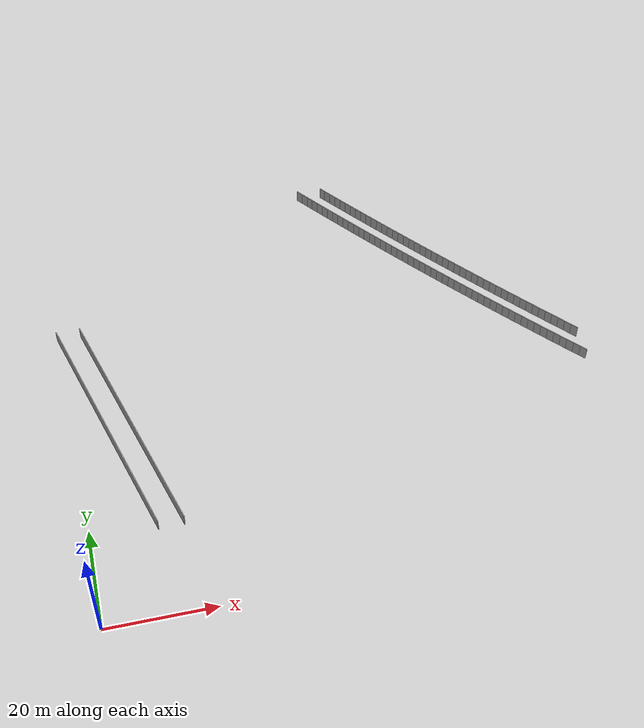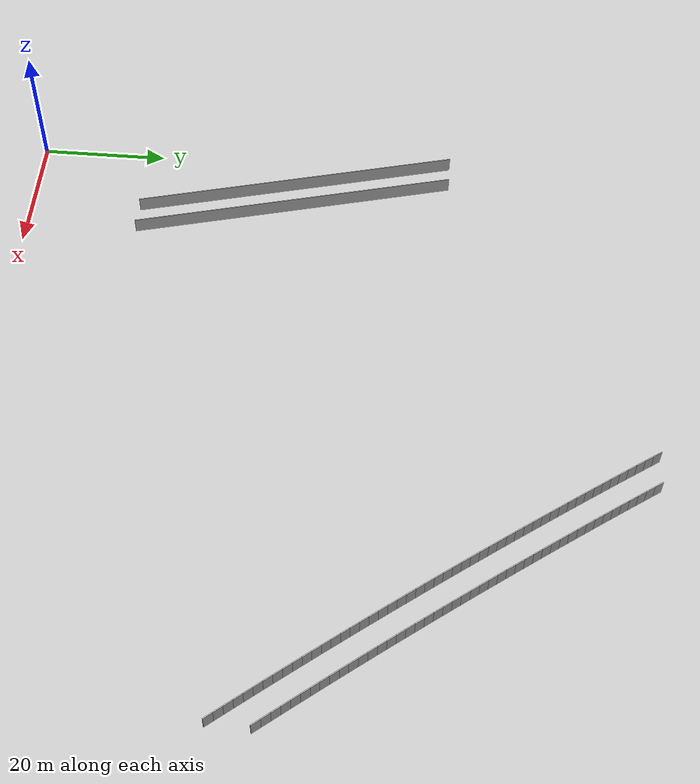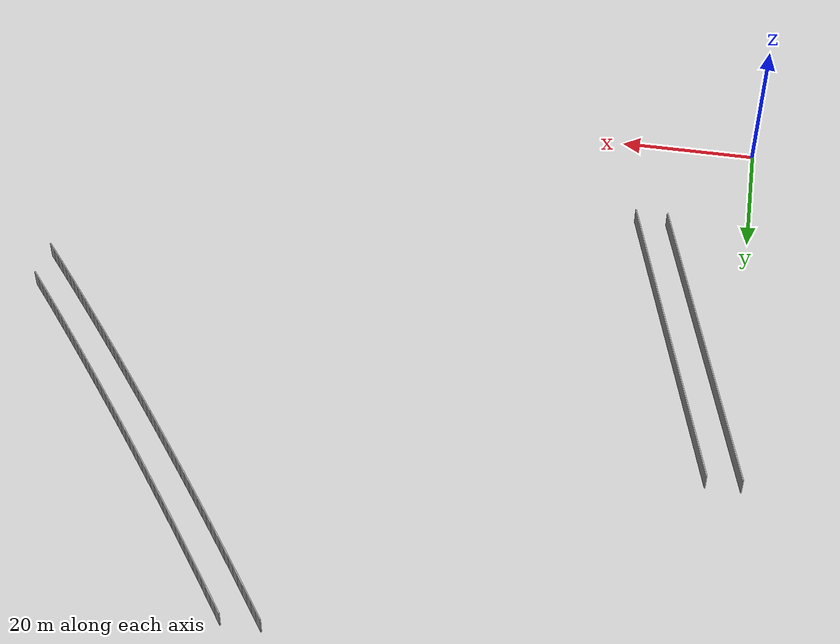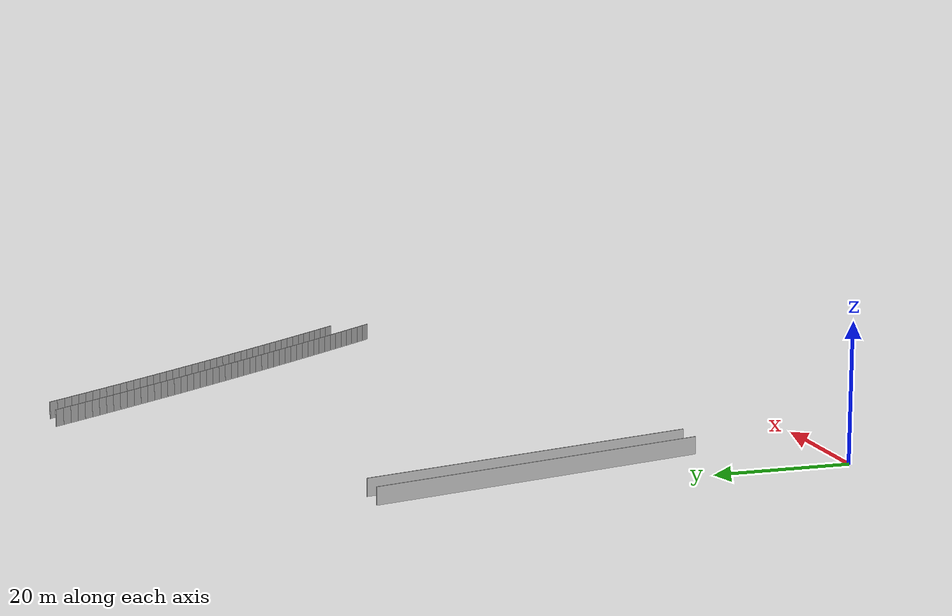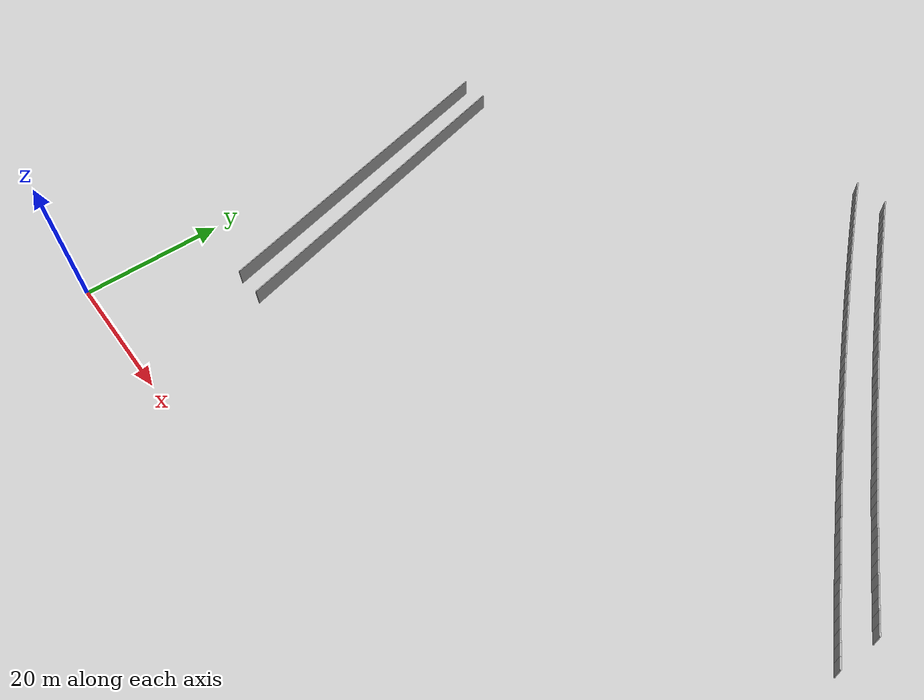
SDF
<?xml version="1.0" ?>
<sdf version="1.6">
  <model name="sps_0305">
    <pose frame="">0 0 0 0 -0 0</pose>
    <static>1</static>
    <self_collide>0</self_collide>
    <allow_auto_disable>0</allow_auto_disable>
    <link name="Wall99">
      <kinematic>0</kinematic>
      <gravity>1</gravity>
      <self_collide>0</self_collide>
      <collision name="collision">
        <geometry>
          <box>
            <size>51.7448 0.15 2.5</size>
          </box>
        </geometry>
        <pose frame="">0 0 0 0 -0 0</pose>
      </collision>
      <visual name="visual">
        <geometry>
          <box>
            <size>51.7448 0.15 2.5</size>
          </box>
        </geometry>
        <pose frame="">0 0 0 0 -0 0</pose>
        <cast_shadows>1</cast_shadows>
        <transparency>0.0</transparency>
      </visual>
      <pose frame="">10.0177 42.8931 1.25 0 -0 1.83122</pose>
    </link>
    <link name="Wall505">
      <kinematic>0</kinematic>
      <gravity>1</gravity>
      <self_collide>0</self_collide>
      <collision name="collision">
        <geometry>
          <box>
            <size>51.7448 0.15 2.5</size>
          </box>
        </geometry>
        <pose frame="">0 0 0 0 -0 0</pose>
      </collision>
      <visual name="visual">
        <geometry>
          <box>
            <size>51.7448 0.15 2.5</size>
          </box>
        </geometry>
        <pose frame="">0 0 0 0 -0 0</pose>
        <cast_shadows>1</cast_shadows>
        <transparency>0.0</transparency>
      </visual>
      <pose frame="">5.35985 42.8931 1.25 0 -0 1.83122</pose>
    </link>
    <link name="Wall8441">
      <kinematic>0</kinematic>
      <gravity>1</gravity>
      <self_collide>0</self_collide>
      <collision name="collision">
        <geometry>
          <box>
            <size>1.49896 0.15 2.5</size>
          </box>
        </geometry>
        <pose frame="">0 0 0 0 -0 0</pose>
      </collision>
      <visual name="visual">
        <geometry>
          <box>
            <size>1.49896 0.15 2.5</size>
          </box>
        </geometry>
        <pose frame="">0 0 0 0 -0 0</pose>
        <cast_shadows>1</cast_shadows>
        <transparency>0.0</transparency>
      </visual>
      <pose frame="">55.0629 99.0742 1.25 0 0 -0.961245</pose>
    </link>
    <link name="Wall8442">
      <kinematic>0</kinematic>
      <gravity>1</gravity>
      <self_collide>0</self_collide>
      <collision name="collision">
        <geometry>
          <box>
            <size>1.49904 0.15 2.5</size>
          </box>
        </geometry>
        <pose frame="">0 0 0 0 -0 0</pose>
      </collision>
      <visual name="visual">
        <geometry>
          <box>
            <size>1.49904 0.15 2.5</size>
          </box>
        </geometry>
        <pose frame="">0 0 0 0 -0 0</pose>
        <cast_shadows>1</cast_shadows>
        <transparency>0.0</transparency>
      </visual>
      <pose frame="">55.922 97.8458 1.25 0 0 -0.959743</pose>
    </link>
    <link name="Wall8443">
      <kinematic>0</kinematic>
      <gravity>1</gravity>
      <self_collide>0</self_collide>
      <collision name="collision">
        <geometry>
          <box>
            <size>1.49888 0.15 2.5</size>
          </box>
        </geometry>
        <pose frame="">0 0 0 0 -0 0</pose>
      </collision>
      <visual name="visual">
        <geometry>
          <box>
            <size>1.49888 0.15 2.5</size>
          </box>
        </geometry>
        <pose frame="">0 0 0 0 -0 0</pose>
        <cast_shadows>1</cast_shadows>
        <transparency>0.0</transparency>
      </visual>
      <pose frame="">56.783 96.6187 1.25 0 0 -0.958272</pose>
    </link>
    <link name="Wall8444">
      <kinematic>0</kinematic>
      <gravity>1</gravity>
      <self_collide>0</self_collide>
      <collision name="collision">
        <geometry>
          <box>
            <size>1.49908 0.15 2.5</size>
          </box>
        </geometry>
        <pose frame="">0 0 0 0 -0 0</pose>
      </collision>
      <visual name="visual">
        <geometry>
          <box>
            <size>1.49908 0.15 2.5</size>
          </box>
        </geometry>
        <pose frame="">0 0 0 0 -0 0</pose>
        <cast_shadows>1</cast_shadows>
        <transparency>0.0</transparency>
      </visual>
      <pose frame="">57.6458 95.393 1.25 0 0 -0.956525</pose>
    </link>
    <link name="Wall8445">
      <kinematic>0</kinematic>
      <gravity>1</gravity>
      <self_collide>0</self_collide>
      <collision name="collision">
        <geometry>
          <box>
            <size>1.4988 0.15 2.5</size>
          </box>
        </geometry>
        <pose frame="">0 0 0 0 -0 0</pose>
      </collision>
      <visual name="visual">
        <geometry>
          <box>
            <size>1.4988 0.15 2.5</size>
          </box>
        </geometry>
        <pose frame="">0 0 0 0 -0 0</pose>
        <cast_shadows>1</cast_shadows>
        <transparency>0.0</transparency>
      </visual>
      <pose frame="">58.5106 94.1687 1.25 0 0 -0.955096</pose>
    </link>
    <link name="Wall8446">
      <kinematic>0</kinematic>
      <gravity>1</gravity>
      <self_collide>0</self_collide>
      <collision name="collision">
        <geometry>
          <box>
            <size>1.49897 0.15 2.5</size>
          </box>
        </geometry>
        <pose frame="">0 0 0 0 -0 0</pose>
      </collision>
      <visual name="visual">
        <geometry>
          <box>
            <size>1.49897 0.15 2.5</size>
          </box>
        </geometry>
        <pose frame="">0 0 0 0 -0 0</pose>
        <cast_shadows>1</cast_shadows>
        <transparency>0.0</transparency>
      </visual>
      <pose frame="">59.3773 92.9458 1.25 0 0 -0.953382</pose>
    </link>
    <link name="Wall8447">
      <kinematic>0</kinematic>
      <gravity>1</gravity>
      <self_collide>0</self_collide>
      <collision name="collision">
        <geometry>
          <box>
            <size>1.49895 0.15 2.5</size>
          </box>
        </geometry>
        <pose frame="">0 0 0 0 -0 0</pose>
      </collision>
      <visual name="visual">
        <geometry>
          <box>
            <size>1.49895 0.15 2.5</size>
          </box>
        </geometry>
        <pose frame="">0 0 0 0 -0 0</pose>
        <cast_shadows>1</cast_shadows>
        <transparency>0.0</transparency>
      </visual>
      <pose frame="">60.2461 91.7243 1.25 0 0 -0.951721</pose>
    </link>
    <link name="Wall8448">
      <kinematic>0</kinematic>
      <gravity>1</gravity>
      <self_collide>0</self_collide>
      <collision name="collision">
        <geometry>
          <box>
            <size>1.49863 0.15 2.5</size>
          </box>
        </geometry>
        <pose frame="">0 0 0 0 -0 0</pose>
      </collision>
      <visual name="visual">
        <geometry>
          <box>
            <size>1.49863 0.15 2.5</size>
          </box>
        </geometry>
        <pose frame="">0 0 0 0 -0 0</pose>
        <cast_shadows>1</cast_shadows>
        <transparency>0.0</transparency>
      </visual>
      <pose frame="">61.1168 90.5043 1.25 0 0 -0.950268</pose>
    </link>
    <link name="Wall8449">
      <kinematic>0</kinematic>
      <gravity>1</gravity>
      <self_collide>0</self_collide>
      <collision name="collision">
        <geometry>
          <box>
            <size>1.49886 0.15 2.5</size>
          </box>
        </geometry>
        <pose frame="">0 0 0 0 -0 0</pose>
      </collision>
      <visual name="visual">
        <geometry>
          <box>
            <size>1.49886 0.15 2.5</size>
          </box>
        </geometry>
        <pose frame="">0 0 0 0 -0 0</pose>
        <cast_shadows>1</cast_shadows>
        <transparency>0.0</transparency>
      </visual>
      <pose frame="">61.9892 89.2857 1.25 0 0 -0.948578</pose>
    </link>
    <link name="Wall8450">
      <kinematic>0</kinematic>
      <gravity>1</gravity>
      <self_collide>0</self_collide>
      <collision name="collision">
        <geometry>
          <box>
            <size>1.49884 0.15 2.5</size>
          </box>
        </geometry>
        <pose frame="">0 0 0 0 -0 0</pose>
      </collision>
      <visual name="visual">
        <geometry>
          <box>
            <size>1.49884 0.15 2.5</size>
          </box>
        </geometry>
        <pose frame="">0 0 0 0 -0 0</pose>
        <cast_shadows>1</cast_shadows>
        <transparency>0.0</transparency>
      </visual>
      <pose frame="">62.8638 88.0684 1.25 0 0 -0.947063</pose>
    </link>
    <link name="Wall8451">
      <kinematic>0</kinematic>
      <gravity>1</gravity>
      <self_collide>0</self_collide>
      <collision name="collision">
        <geometry>
          <box>
            <size>1.49899 0.15 2.5</size>
          </box>
        </geometry>
        <pose frame="">0 0 0 0 -0 0</pose>
      </collision>
      <visual name="visual">
        <geometry>
          <box>
            <size>1.49899 0.15 2.5</size>
          </box>
        </geometry>
        <pose frame="">0 0 0 0 -0 0</pose>
        <cast_shadows>1</cast_shadows>
        <transparency>0.0</transparency>
      </visual>
      <pose frame="">63.7402 86.8524 1.25 0 0 -0.94553</pose>
    </link>
    <link name="Wall8452">
      <kinematic>0</kinematic>
      <gravity>1</gravity>
      <self_collide>0</self_collide>
      <collision name="collision">
        <geometry>
          <box>
            <size>1.49903 0.15 2.5</size>
          </box>
        </geometry>
        <pose frame="">0 0 0 0 -0 0</pose>
      </collision>
      <visual name="visual">
        <geometry>
          <box>
            <size>1.49903 0.15 2.5</size>
          </box>
        </geometry>
        <pose frame="">0 0 0 0 -0 0</pose>
        <cast_shadows>1</cast_shadows>
        <transparency>0.0</transparency>
      </visual>
      <pose frame="">64.6186 85.6377 1.25 0 0 -0.943892</pose>
    </link>
    <link name="Wall8453">
      <kinematic>0</kinematic>
      <gravity>1</gravity>
      <self_collide>0</self_collide>
      <collision name="collision">
        <geometry>
          <box>
            <size>1.49902 0.15 2.5</size>
          </box>
        </geometry>
        <pose frame="">0 0 0 0 -0 0</pose>
      </collision>
      <visual name="visual">
        <geometry>
          <box>
            <size>1.49902 0.15 2.5</size>
          </box>
        </geometry>
        <pose frame="">0 0 0 0 -0 0</pose>
        <cast_shadows>1</cast_shadows>
        <transparency>0.0</transparency>
      </visual>
      <pose frame="">65.4989 84.4244 1.25 0 0 -0.942377</pose>
    </link>
    <link name="Wall8454">
      <kinematic>0</kinematic>
      <gravity>1</gravity>
      <self_collide>0</self_collide>
      <collision name="collision">
        <geometry>
          <box>
            <size>1.49888 0.15 2.5</size>
          </box>
        </geometry>
        <pose frame="">0 0 0 0 -0 0</pose>
      </collision>
      <visual name="visual">
        <geometry>
          <box>
            <size>1.49888 0.15 2.5</size>
          </box>
        </geometry>
        <pose frame="">0 0 0 0 -0 0</pose>
        <cast_shadows>1</cast_shadows>
        <transparency>0.0</transparency>
      </visual>
      <pose frame="">66.381 83.2125 1.25 0 0 -0.940847</pose>
    </link>
    <link name="Wall8455">
      <kinematic>0</kinematic>
      <gravity>1</gravity>
      <self_collide>0</self_collide>
      <collision name="collision">
        <geometry>
          <box>
            <size>1.49879 0.15 2.5</size>
          </box>
        </geometry>
        <pose frame="">0 0 0 0 -0 0</pose>
      </collision>
      <visual name="visual">
        <geometry>
          <box>
            <size>1.49879 0.15 2.5</size>
          </box>
        </geometry>
        <pose frame="">0 0 0 0 -0 0</pose>
        <cast_shadows>1</cast_shadows>
        <transparency>0.0</transparency>
      </visual>
      <pose frame="">67.265 82.0021 1.25 0 0 -0.939138</pose>
    </link>
    <link name="Wall8456">
      <kinematic>0</kinematic>
      <gravity>1</gravity>
      <self_collide>0</self_collide>
      <collision name="collision">
        <geometry>
          <box>
            <size>1.49896 0.15 2.5</size>
          </box>
        </geometry>
        <pose frame="">0 0 0 0 -0 0</pose>
      </collision>
      <visual name="visual">
        <geometry>
          <box>
            <size>1.49896 0.15 2.5</size>
          </box>
        </geometry>
        <pose frame="">0 0 0 0 -0 0</pose>
        <cast_shadows>1</cast_shadows>
        <transparency>0.0</transparency>
      </visual>
      <pose frame="">68.151 80.7931 1.25 0 0 -0.937605</pose>
    </link>
    <link name="Wall8457">
      <kinematic>0</kinematic>
      <gravity>1</gravity>
      <self_collide>0</self_collide>
      <collision name="collision">
        <geometry>
          <box>
            <size>1.49911 0.15 2.5</size>
          </box>
        </geometry>
        <pose frame="">0 0 0 0 -0 0</pose>
      </collision>
      <visual name="visual">
        <geometry>
          <box>
            <size>1.49911 0.15 2.5</size>
          </box>
        </geometry>
        <pose frame="">0 0 0 0 -0 0</pose>
        <cast_shadows>1</cast_shadows>
        <transparency>0.0</transparency>
      </visual>
      <pose frame="">69.0388 79.5853 1.25 0 0 -0.936163</pose>
    </link>
    <link name="Wall8458">
      <kinematic>0</kinematic>
      <gravity>1</gravity>
      <self_collide>0</self_collide>
      <collision name="collision">
        <geometry>
          <box>
            <size>1.49903 0.15 2.5</size>
          </box>
        </geometry>
        <pose frame="">0 0 0 0 -0 0</pose>
      </collision>
      <visual name="visual">
        <geometry>
          <box>
            <size>1.49903 0.15 2.5</size>
          </box>
        </geometry>
        <pose frame="">0 0 0 0 -0 0</pose>
        <cast_shadows>1</cast_shadows>
        <transparency>0.0</transparency>
      </visual>
      <pose frame="">69.9286 78.3789 1.25 0 0 -0.934453</pose>
    </link>
    <link name="Wall8459">
      <kinematic>0</kinematic>
      <gravity>1</gravity>
      <self_collide>0</self_collide>
      <collision name="collision">
        <geometry>
          <box>
            <size>1.49894 0.15 2.5</size>
          </box>
        </geometry>
        <pose frame="">0 0 0 0 -0 0</pose>
      </collision>
      <visual name="visual">
        <geometry>
          <box>
            <size>1.49894 0.15 2.5</size>
          </box>
        </geometry>
        <pose frame="">0 0 0 0 -0 0</pose>
        <cast_shadows>1</cast_shadows>
        <transparency>0.0</transparency>
      </visual>
      <pose frame="">70.8204 77.174 1.25 0 0 -0.93289</pose>
    </link>
    <link name="Wall8460">
      <kinematic>0</kinematic>
      <gravity>1</gravity>
      <self_collide>0</self_collide>
      <collision name="collision">
        <geometry>
          <box>
            <size>1.49902 0.15 2.5</size>
          </box>
        </geometry>
        <pose frame="">0 0 0 0 -0 0</pose>
      </collision>
      <visual name="visual">
        <geometry>
          <box>
            <size>1.49902 0.15 2.5</size>
          </box>
        </geometry>
        <pose frame="">0 0 0 0 -0 0</pose>
        <cast_shadows>1</cast_shadows>
        <transparency>0.0</transparency>
      </visual>
      <pose frame="">71.714 75.9705 1.25 0 0 -0.93131</pose>
    </link>
    <link name="Wall8461">
      <kinematic>0</kinematic>
      <gravity>1</gravity>
      <self_collide>0</self_collide>
      <collision name="collision">
        <geometry>
          <box>
            <size>1.49895 0.15 2.5</size>
          </box>
        </geometry>
        <pose frame="">0 0 0 0 -0 0</pose>
      </collision>
      <visual name="visual">
        <geometry>
          <box>
            <size>1.49895 0.15 2.5</size>
          </box>
        </geometry>
        <pose frame="">0 0 0 0 -0 0</pose>
        <cast_shadows>1</cast_shadows>
        <transparency>0.0</transparency>
      </visual>
      <pose frame="">72.6095 74.7684 1.25 0 0 -0.929803</pose>
    </link>
    <link name="Wall8462">
      <kinematic>0</kinematic>
      <gravity>1</gravity>
      <self_collide>0</self_collide>
      <collision name="collision">
        <geometry>
          <box>
            <size>1.49907 0.15 2.5</size>
          </box>
        </geometry>
        <pose frame="">0 0 0 0 -0 0</pose>
      </collision>
      <visual name="visual">
        <geometry>
          <box>
            <size>1.49907 0.15 2.5</size>
          </box>
        </geometry>
        <pose frame="">0 0 0 0 -0 0</pose>
        <cast_shadows>1</cast_shadows>
        <transparency>0.0</transparency>
      </visual>
      <pose frame="">73.5069 73.5677 1.25 0 0 -0.928134</pose>
    </link>
    <link name="Wall8463">
      <kinematic>0</kinematic>
      <gravity>1</gravity>
      <self_collide>0</self_collide>
      <collision name="collision">
        <geometry>
          <box>
            <size>1.49893 0.15 2.5</size>
          </box>
        </geometry>
        <pose frame="">0 0 0 0 -0 0</pose>
      </collision>
      <visual name="visual">
        <geometry>
          <box>
            <size>1.49893 0.15 2.5</size>
          </box>
        </geometry>
        <pose frame="">0 0 0 0 -0 0</pose>
        <cast_shadows>1</cast_shadows>
        <transparency>0.0</transparency>
      </visual>
      <pose frame="">74.4063 72.3685 1.25 0 0 -0.926432</pose>
    </link>
    <link name="Wall8464">
      <kinematic>0</kinematic>
      <gravity>1</gravity>
      <self_collide>0</self_collide>
      <collision name="collision">
        <geometry>
          <box>
            <size>1.49892 0.15 2.5</size>
          </box>
        </geometry>
        <pose frame="">0 0 0 0 -0 0</pose>
      </collision>
      <visual name="visual">
        <geometry>
          <box>
            <size>1.49892 0.15 2.5</size>
          </box>
        </geometry>
        <pose frame="">0 0 0 0 -0 0</pose>
        <cast_shadows>1</cast_shadows>
        <transparency>0.0</transparency>
      </visual>
      <pose frame="">75.3075 71.1708 1.25 0 0 -0.92495</pose>
    </link>
    <link name="Wall8465">
      <kinematic>0</kinematic>
      <gravity>1</gravity>
      <self_collide>0</self_collide>
      <collision name="collision">
        <geometry>
          <box>
            <size>1.49889 0.15 2.5</size>
          </box>
        </geometry>
        <pose frame="">0 0 0 0 -0 0</pose>
      </collision>
      <visual name="visual">
        <geometry>
          <box>
            <size>1.49889 0.15 2.5</size>
          </box>
        </geometry>
        <pose frame="">0 0 0 0 -0 0</pose>
        <cast_shadows>1</cast_shadows>
        <transparency>0.0</transparency>
      </visual>
      <pose frame="">76.2107 69.9745 1.25 0 0 -0.923353</pose>
    </link>
    <link name="Wall8466">
      <kinematic>0</kinematic>
      <gravity>1</gravity>
      <self_collide>0</self_collide>
      <collision name="collision">
        <geometry>
          <box>
            <size>1.49885 0.15 2.5</size>
          </box>
        </geometry>
        <pose frame="">0 0 0 0 -0 0</pose>
      </collision>
      <visual name="visual">
        <geometry>
          <box>
            <size>1.49885 0.15 2.5</size>
          </box>
        </geometry>
        <pose frame="">0 0 0 0 -0 0</pose>
        <cast_shadows>1</cast_shadows>
        <transparency>0.0</transparency>
      </visual>
      <pose frame="">77.1156 68.7796 1.25 0 0 -0.921904</pose>
    </link>
    <link name="Wall8467">
      <kinematic>0</kinematic>
      <gravity>1</gravity>
      <self_collide>0</self_collide>
      <collision name="collision">
        <geometry>
          <box>
            <size>1.49884 0.15 2.5</size>
          </box>
        </geometry>
        <pose frame="">0 0 0 0 -0 0</pose>
      </collision>
      <visual name="visual">
        <geometry>
          <box>
            <size>1.49884 0.15 2.5</size>
          </box>
        </geometry>
        <pose frame="">0 0 0 0 -0 0</pose>
        <cast_shadows>1</cast_shadows>
        <transparency>0.0</transparency>
      </visual>
      <pose frame="">78.0224 67.5862 1.25 0 0 -0.920161</pose>
    </link>
    <link name="Wall8468">
      <kinematic>0</kinematic>
      <gravity>1</gravity>
      <self_collide>0</self_collide>
      <collision name="collision">
        <geometry>
          <box>
            <size>1.49906 0.15 2.5</size>
          </box>
        </geometry>
        <pose frame="">0 0 0 0 -0 0</pose>
      </collision>
      <visual name="visual">
        <geometry>
          <box>
            <size>1.49906 0.15 2.5</size>
          </box>
        </geometry>
        <pose frame="">0 0 0 0 -0 0</pose>
        <cast_shadows>1</cast_shadows>
        <transparency>0.0</transparency>
      </visual>
      <pose frame="">78.9312 66.3942 1.25 0 0 -0.918631</pose>
    </link>
    <link name="Wall8469">
      <kinematic>0</kinematic>
      <gravity>1</gravity>
      <self_collide>0</self_collide>
      <collision name="collision">
        <geometry>
          <box>
            <size>1.49902 0.15 2.5</size>
          </box>
        </geometry>
        <pose frame="">0 0 0 0 -0 0</pose>
      </collision>
      <visual name="visual">
        <geometry>
          <box>
            <size>1.49902 0.15 2.5</size>
          </box>
        </geometry>
        <pose frame="">0 0 0 0 -0 0</pose>
        <cast_shadows>1</cast_shadows>
        <transparency>0.0</transparency>
      </visual>
      <pose frame="">79.8418 65.2035 1.25 0 0 -0.917124</pose>
    </link>
    <link name="Wall8470">
      <kinematic>0</kinematic>
      <gravity>1</gravity>
      <self_collide>0</self_collide>
      <collision name="collision">
        <geometry>
          <box>
            <size>1.49886 0.15 2.5</size>
          </box>
        </geometry>
        <pose frame="">0 0 0 0 -0 0</pose>
      </collision>
      <visual name="visual">
        <geometry>
          <box>
            <size>1.49886 0.15 2.5</size>
          </box>
        </geometry>
        <pose frame="">0 0 0 0 -0 0</pose>
        <cast_shadows>1</cast_shadows>
        <transparency>0.0</transparency>
      </visual>
      <pose frame="">80.7544 64.0143 1.25 0 0 -0.915453</pose>
    </link>
    <link name="Wall8471">
      <kinematic>0</kinematic>
      <gravity>1</gravity>
      <self_collide>0</self_collide>
      <collision name="collision">
        <geometry>
          <box>
            <size>1.49895 0.15 2.5</size>
          </box>
        </geometry>
        <pose frame="">0 0 0 0 -0 0</pose>
      </collision>
      <visual name="visual">
        <geometry>
          <box>
            <size>1.49895 0.15 2.5</size>
          </box>
        </geometry>
        <pose frame="">0 0 0 0 -0 0</pose>
        <cast_shadows>1</cast_shadows>
        <transparency>0.0</transparency>
      </visual>
      <pose frame="">81.6688 62.8266 1.25 0 0 -0.913907</pose>
    </link>
    <link name="Wall8472">
      <kinematic>0</kinematic>
      <gravity>1</gravity>
      <self_collide>0</self_collide>
      <collision name="collision">
        <geometry>
          <box>
            <size>1.499 0.15 2.5</size>
          </box>
        </geometry>
        <pose frame="">0 0 0 0 -0 0</pose>
      </collision>
      <visual name="visual">
        <geometry>
          <box>
            <size>1.499 0.15 2.5</size>
          </box>
        </geometry>
        <pose frame="">0 0 0 0 -0 0</pose>
        <cast_shadows>1</cast_shadows>
        <transparency>0.0</transparency>
      </visual>
      <pose frame="">82.585 61.6403 1.25 0 0 -0.912335</pose>
    </link>
    <link name="Wall8473">
      <kinematic>0</kinematic>
      <gravity>1</gravity>
      <self_collide>0</self_collide>
      <collision name="collision">
        <geometry>
          <box>
            <size>1.49897 0.15 2.5</size>
          </box>
        </geometry>
        <pose frame="">0 0 0 0 -0 0</pose>
      </collision>
      <visual name="visual">
        <geometry>
          <box>
            <size>1.49897 0.15 2.5</size>
          </box>
        </geometry>
        <pose frame="">0 0 0 0 -0 0</pose>
        <cast_shadows>1</cast_shadows>
        <transparency>0.0</transparency>
      </visual>
      <pose frame="">83.5032 60.4554 1.25 0 0 -0.910828</pose>
    </link>
    <link name="Wall8474">
      <kinematic>0</kinematic>
      <gravity>1</gravity>
      <self_collide>0</self_collide>
      <collision name="collision">
        <geometry>
          <box>
            <size>1.49892 0.15 2.5</size>
          </box>
        </geometry>
        <pose frame="">0 0 0 0 -0 0</pose>
      </collision>
      <visual name="visual">
        <geometry>
          <box>
            <size>1.49892 0.15 2.5</size>
          </box>
        </geometry>
        <pose frame="">0 0 0 0 -0 0</pose>
        <cast_shadows>1</cast_shadows>
        <transparency>0.0</transparency>
      </visual>
      <pose frame="">84.4231 59.272 1.25 0 0 -0.90915</pose>
    </link>
    <link name="Wall8475">
      <kinematic>0</kinematic>
      <gravity>1</gravity>
      <self_collide>0</self_collide>
      <collision name="collision">
        <geometry>
          <box>
            <size>1.49878 0.15 2.5</size>
          </box>
        </geometry>
        <pose frame="">0 0 0 0 -0 0</pose>
      </collision>
      <visual name="visual">
        <geometry>
          <box>
            <size>1.49878 0.15 2.5</size>
          </box>
        </geometry>
        <pose frame="">0 0 0 0 -0 0</pose>
        <cast_shadows>1</cast_shadows>
        <transparency>0.0</transparency>
      </visual>
      <pose frame="">85.3451 58.0902 1.25 0 0 -0.907478</pose>
    </link>
    <link name="Wall8476">
      <kinematic>0</kinematic>
      <gravity>1</gravity>
      <self_collide>0</self_collide>
      <collision name="collision">
        <geometry>
          <box>
            <size>1.49892 0.15 2.5</size>
          </box>
        </geometry>
        <pose frame="">0 0 0 0 -0 0</pose>
      </collision>
      <visual name="visual">
        <geometry>
          <box>
            <size>1.49892 0.15 2.5</size>
          </box>
        </geometry>
        <pose frame="">0 0 0 0 -0 0</pose>
        <cast_shadows>1</cast_shadows>
        <transparency>0.0</transparency>
      </visual>
      <pose frame="">86.2688 56.9098 1.25 0 0 -0.906103</pose>
    </link>
    <link name="Wall8477">
      <kinematic>0</kinematic>
      <gravity>1</gravity>
      <self_collide>0</self_collide>
      <collision name="collision">
        <geometry>
          <box>
            <size>1.49895 0.15 2.5</size>
          </box>
        </geometry>
        <pose frame="">0 0 0 0 -0 0</pose>
      </collision>
      <visual name="visual">
        <geometry>
          <box>
            <size>1.49895 0.15 2.5</size>
          </box>
        </geometry>
        <pose frame="">0 0 0 0 -0 0</pose>
        <cast_shadows>1</cast_shadows>
        <transparency>0.0</transparency>
      </visual>
      <pose frame="">87.1944 55.7308 1.25 0 0 -0.904361</pose>
    </link>
    <link name="Wall8478">
      <kinematic>0</kinematic>
      <gravity>1</gravity>
      <self_collide>0</self_collide>
      <collision name="collision">
        <geometry>
          <box>
            <size>1.49875 0.15 2.5</size>
          </box>
        </geometry>
        <pose frame="">0 0 0 0 -0 0</pose>
      </collision>
      <visual name="visual">
        <geometry>
          <box>
            <size>1.49875 0.15 2.5</size>
          </box>
        </geometry>
        <pose frame="">0 0 0 0 -0 0</pose>
        <cast_shadows>1</cast_shadows>
        <transparency>0.0</transparency>
      </visual>
      <pose frame="">88.1218 54.5533 1.25 0 0 -0.902956</pose>
    </link>
    <link name="Wall8479">
      <kinematic>0</kinematic>
      <gravity>1</gravity>
      <self_collide>0</self_collide>
      <collision name="collision">
        <geometry>
          <box>
            <size>1.49909 0.15 2.5</size>
          </box>
        </geometry>
        <pose frame="">0 0 0 0 -0 0</pose>
      </collision>
      <visual name="visual">
        <geometry>
          <box>
            <size>1.49909 0.15 2.5</size>
          </box>
        </geometry>
        <pose frame="">0 0 0 0 -0 0</pose>
        <cast_shadows>1</cast_shadows>
        <transparency>0.0</transparency>
      </visual>
      <pose frame="">89.051 53.3772 1.25 0 0 -0.901219</pose>
    </link>
    <link name="Wall8480">
      <kinematic>0</kinematic>
      <gravity>1</gravity>
      <self_collide>0</self_collide>
      <collision name="collision">
        <geometry>
          <box>
            <size>1.49884 0.15 2.5</size>
          </box>
        </geometry>
        <pose frame="">0 0 0 0 -0 0</pose>
      </collision>
      <visual name="visual">
        <geometry>
          <box>
            <size>1.49884 0.15 2.5</size>
          </box>
        </geometry>
        <pose frame="">0 0 0 0 -0 0</pose>
        <cast_shadows>1</cast_shadows>
        <transparency>0.0</transparency>
      </visual>
      <pose frame="">89.9823 52.2026 1.25 0 0 -0.899731</pose>
    </link>
    <link name="Wall8481">
      <kinematic>0</kinematic>
      <gravity>1</gravity>
      <self_collide>0</self_collide>
      <collision name="collision">
        <geometry>
          <box>
            <size>1.49913 0.15 2.5</size>
          </box>
        </geometry>
        <pose frame="">0 0 0 0 -0 0</pose>
      </collision>
      <visual name="visual">
        <geometry>
          <box>
            <size>1.49913 0.15 2.5</size>
          </box>
        </geometry>
        <pose frame="">0 0 0 0 -0 0</pose>
        <cast_shadows>1</cast_shadows>
        <transparency>0.0</transparency>
      </visual>
      <pose frame="">90.9153 51.0294 1.25 0 0 -0.898173</pose>
    </link>
    <link name="Wall8482">
      <kinematic>0</kinematic>
      <gravity>1</gravity>
      <self_collide>0</self_collide>
      <collision name="collision">
        <geometry>
          <box>
            <size>1.49895 0.15 2.5</size>
          </box>
        </geometry>
        <pose frame="">0 0 0 0 -0 0</pose>
      </collision>
      <visual name="visual">
        <geometry>
          <box>
            <size>1.49895 0.15 2.5</size>
          </box>
        </geometry>
        <pose frame="">0 0 0 0 -0 0</pose>
        <cast_shadows>1</cast_shadows>
        <transparency>0.0</transparency>
      </visual>
      <pose frame="">91.8502 49.8576 1.25 0 0 -0.896564</pose>
    </link>
    <link name="Wall8483">
      <kinematic>0</kinematic>
      <gravity>1</gravity>
      <self_collide>0</self_collide>
      <collision name="collision">
        <geometry>
          <box>
            <size>1.49902 0.15 2.5</size>
          </box>
        </geometry>
        <pose frame="">0 0 0 0 -0 0</pose>
      </collision>
      <visual name="visual">
        <geometry>
          <box>
            <size>1.49902 0.15 2.5</size>
          </box>
        </geometry>
        <pose frame="">0 0 0 0 -0 0</pose>
        <cast_shadows>1</cast_shadows>
        <transparency>0.0</transparency>
      </visual>
      <pose frame="">92.787 48.6874 1.25 0 0 -0.894879</pose>
    </link>
    <link name="Wall8484">
      <kinematic>0</kinematic>
      <gravity>1</gravity>
      <self_collide>0</self_collide>
      <collision name="collision">
        <geometry>
          <box>
            <size>1.49887 0.15 2.5</size>
          </box>
        </geometry>
        <pose frame="">0 0 0 0 -0 0</pose>
      </collision>
      <visual name="visual">
        <geometry>
          <box>
            <size>1.49887 0.15 2.5</size>
          </box>
        </geometry>
        <pose frame="">0 0 0 0 -0 0</pose>
        <cast_shadows>1</cast_shadows>
        <transparency>0.0</transparency>
      </visual>
      <pose frame="">93.7256 47.5187 1.25 0 0 -0.893442</pose>
    </link>
    <link name="Wall8485">
      <kinematic>0</kinematic>
      <gravity>1</gravity>
      <self_collide>0</self_collide>
      <collision name="collision">
        <geometry>
          <box>
            <size>1.49894 0.15 2.5</size>
          </box>
        </geometry>
        <pose frame="">0 0 0 0 -0 0</pose>
      </collision>
      <visual name="visual">
        <geometry>
          <box>
            <size>1.49894 0.15 2.5</size>
          </box>
        </geometry>
        <pose frame="">0 0 0 0 -0 0</pose>
        <cast_shadows>1</cast_shadows>
        <transparency>0.0</transparency>
      </visual>
      <pose frame="">94.666 46.3515 1.25 0 0 -0.891757</pose>
    </link>
    <link name="Wall8486">
      <kinematic>0</kinematic>
      <gravity>1</gravity>
      <self_collide>0</self_collide>
      <collision name="collision">
        <geometry>
          <box>
            <size>1.49892 0.15 2.5</size>
          </box>
        </geometry>
        <pose frame="">0 0 0 0 -0 0</pose>
      </collision>
      <visual name="visual">
        <geometry>
          <box>
            <size>1.49892 0.15 2.5</size>
          </box>
        </geometry>
        <pose frame="">0 0 0 0 -0 0</pose>
        <cast_shadows>1</cast_shadows>
        <transparency>0.0</transparency>
      </visual>
      <pose frame="">95.6083 45.1858 1.25 0 0 -0.890224</pose>
    </link>
    <link name="Wall8487">
      <kinematic>0</kinematic>
      <gravity>1</gravity>
      <self_collide>0</self_collide>
      <collision name="collision">
        <geometry>
          <box>
            <size>1.49884 0.15 2.5</size>
          </box>
        </geometry>
        <pose frame="">0 0 0 0 -0 0</pose>
      </collision>
      <visual name="visual">
        <geometry>
          <box>
            <size>1.49884 0.15 2.5</size>
          </box>
        </geometry>
        <pose frame="">0 0 0 0 -0 0</pose>
        <cast_shadows>1</cast_shadows>
        <transparency>0.0</transparency>
      </visual>
      <pose frame="">96.5524 44.0216 1.25 0 0 -0.888608</pose>
    </link>
    <link name="Wall8488">
      <kinematic>0</kinematic>
      <gravity>1</gravity>
      <self_collide>0</self_collide>
      <collision name="collision">
        <geometry>
          <box>
            <size>1.49921 0.15 2.5</size>
          </box>
        </geometry>
        <pose frame="">0 0 0 0 -0 0</pose>
      </collision>
      <visual name="visual">
        <geometry>
          <box>
            <size>1.49921 0.15 2.5</size>
          </box>
        </geometry>
        <pose frame="">0 0 0 0 -0 0</pose>
        <cast_shadows>1</cast_shadows>
        <transparency>0.0</transparency>
      </visual>
      <pose frame="">97.4984 42.8588 1.25 0 0 -0.887078</pose>
    </link>
    <link name="Wall8489">
      <kinematic>0</kinematic>
      <gravity>1</gravity>
      <self_collide>0</self_collide>
      <collision name="collision">
        <geometry>
          <box>
            <size>1.49891 0.15 2.5</size>
          </box>
        </geometry>
        <pose frame="">0 0 0 0 -0 0</pose>
      </collision>
      <visual name="visual">
        <geometry>
          <box>
            <size>1.49891 0.15 2.5</size>
          </box>
        </geometry>
        <pose frame="">0 0 0 0 -0 0</pose>
        <cast_shadows>1</cast_shadows>
        <transparency>0.0</transparency>
      </visual>
      <pose frame="">98.4463 41.6975 1.25 0 0 -0.885391</pose>
    </link>
    <link name="Wall8490">
      <kinematic>0</kinematic>
      <gravity>1</gravity>
      <self_collide>0</self_collide>
      <collision name="collision">
        <geometry>
          <box>
            <size>1.49895 0.15 2.5</size>
          </box>
        </geometry>
        <pose frame="">0 0 0 0 -0 0</pose>
      </collision>
      <visual name="visual">
        <geometry>
          <box>
            <size>1.49895 0.15 2.5</size>
          </box>
        </geometry>
        <pose frame="">0 0 0 0 -0 0</pose>
        <cast_shadows>1</cast_shadows>
        <transparency>0.0</transparency>
      </visual>
      <pose frame="">99.396 40.5378 1.25 0 0 -0.883884</pose>
    </link>
    <link name="Wall9524">
      <kinematic>0</kinematic>
      <gravity>1</gravity>
      <self_collide>0</self_collide>
      <collision name="collision">
        <geometry>
          <box>
            <size>1.49241 0.15 2.5</size>
          </box>
        </geometry>
        <pose frame="">0 0 0 0 -0 0</pose>
      </collision>
      <visual name="visual">
        <geometry>
          <box>
            <size>1.49241 0.15 2.5</size>
          </box>
        </geometry>
        <pose frame="">0 0 0 0 -0 0</pose>
        <cast_shadows>1</cast_shadows>
        <transparency>0.0</transparency>
      </visual>
      <pose frame="">60.1698 98.9998 1.25 0 0 -0.958177</pose>
    </link>
    <link name="Wall9525">
      <kinematic>0</kinematic>
      <gravity>1</gravity>
      <self_collide>0</self_collide>
      <collision name="collision">
        <geometry>
          <box>
            <size>1.49261 0.15 2.5</size>
          </box>
        </geometry>
        <pose frame="">0 0 0 0 -0 0</pose>
      </collision>
      <visual name="visual">
        <geometry>
          <box>
            <size>1.49261 0.15 2.5</size>
          </box>
        </geometry>
        <pose frame="">0 0 0 0 -0 0</pose>
        <cast_shadows>1</cast_shadows>
        <transparency>0.0</transparency>
      </visual>
      <pose frame="">61.029 97.7794 1.25 0 0 -0.95657</pose>
    </link>
    <link name="Wall9526">
      <kinematic>0</kinematic>
      <gravity>1</gravity>
      <self_collide>0</self_collide>
      <collision name="collision">
        <geometry>
          <box>
            <size>1.49233 0.15 2.5</size>
          </box>
        </geometry>
        <pose frame="">0 0 0 0 -0 0</pose>
      </collision>
      <visual name="visual">
        <geometry>
          <box>
            <size>1.49233 0.15 2.5</size>
          </box>
        </geometry>
        <pose frame="">0 0 0 0 -0 0</pose>
        <cast_shadows>1</cast_shadows>
        <transparency>0.0</transparency>
      </visual>
      <pose frame="">61.8901 96.5604 1.25 0 0 -0.954987</pose>
    </link>
    <link name="Wall9527">
      <kinematic>0</kinematic>
      <gravity>1</gravity>
      <self_collide>0</self_collide>
      <collision name="collision">
        <geometry>
          <box>
            <size>1.49255 0.15 2.5</size>
          </box>
        </geometry>
        <pose frame="">0 0 0 0 -0 0</pose>
      </collision>
      <visual name="visual">
        <geometry>
          <box>
            <size>1.49255 0.15 2.5</size>
          </box>
        </geometry>
        <pose frame="">0 0 0 0 -0 0</pose>
        <cast_shadows>1</cast_shadows>
        <transparency>0.0</transparency>
      </visual>
      <pose frame="">62.7531 95.3428 1.25 0 0 -0.953437</pose>
    </link>
    <link name="Wall9528">
      <kinematic>0</kinematic>
      <gravity>1</gravity>
      <self_collide>0</self_collide>
      <collision name="collision">
        <geometry>
          <box>
            <size>1.49234 0.15 2.5</size>
          </box>
        </geometry>
        <pose frame="">0 0 0 0 -0 0</pose>
      </collision>
      <visual name="visual">
        <geometry>
          <box>
            <size>1.49234 0.15 2.5</size>
          </box>
        </geometry>
        <pose frame="">0 0 0 0 -0 0</pose>
        <cast_shadows>1</cast_shadows>
        <transparency>0.0</transparency>
      </visual>
      <pose frame="">63.6181 94.1266 1.25 0 0 -0.951731</pose>
    </link>
    <link name="Wall9529">
      <kinematic>0</kinematic>
      <gravity>1</gravity>
      <self_collide>0</self_collide>
      <collision name="collision">
        <geometry>
          <box>
            <size>1.49241 0.15 2.5</size>
          </box>
        </geometry>
        <pose frame="">0 0 0 0 -0 0</pose>
      </collision>
      <visual name="visual">
        <geometry>
          <box>
            <size>1.49241 0.15 2.5</size>
          </box>
        </geometry>
        <pose frame="">0 0 0 0 -0 0</pose>
        <cast_shadows>1</cast_shadows>
        <transparency>0.0</transparency>
      </visual>
      <pose frame="">64.4849 92.9118 1.25 0 0 -0.950257</pose>
    </link>
    <link name="Wall9530">
      <kinematic>0</kinematic>
      <gravity>1</gravity>
      <self_collide>0</self_collide>
      <collision name="collision">
        <geometry>
          <box>
            <size>1.49238 0.15 2.5</size>
          </box>
        </geometry>
        <pose frame="">0 0 0 0 -0 0</pose>
      </collision>
      <visual name="visual">
        <geometry>
          <box>
            <size>1.49238 0.15 2.5</size>
          </box>
        </geometry>
        <pose frame="">0 0 0 0 -0 0</pose>
        <cast_shadows>1</cast_shadows>
        <transparency>0.0</transparency>
      </visual>
      <pose frame="">65.3537 91.6983 1.25 0 0 -0.948735</pose>
    </link>
    <link name="Wall9531">
      <kinematic>0</kinematic>
      <gravity>1</gravity>
      <self_collide>0</self_collide>
      <collision name="collision">
        <geometry>
          <box>
            <size>1.49193 0.15 2.5</size>
          </box>
        </geometry>
        <pose frame="">0 0 0 0 -0 0</pose>
      </collision>
      <visual name="visual">
        <geometry>
          <box>
            <size>1.49193 0.15 2.5</size>
          </box>
        </geometry>
        <pose frame="">0 0 0 0 -0 0</pose>
        <cast_shadows>1</cast_shadows>
        <transparency>0.0</transparency>
      </visual>
      <pose frame="">66.2242 90.4864 1.25 0 0 -0.947056</pose>
    </link>
    <link name="Wall9532">
      <kinematic>0</kinematic>
      <gravity>1</gravity>
      <self_collide>0</self_collide>
      <collision name="collision">
        <geometry>
          <box>
            <size>1.49237 0.15 2.5</size>
          </box>
        </geometry>
        <pose frame="">0 0 0 0 -0 0</pose>
      </collision>
      <visual name="visual">
        <geometry>
          <box>
            <size>1.49237 0.15 2.5</size>
          </box>
        </geometry>
        <pose frame="">0 0 0 0 -0 0</pose>
        <cast_shadows>1</cast_shadows>
        <transparency>0.0</transparency>
      </visual>
      <pose frame="">67.0967 89.2759 1.25 0 0 -0.945455</pose>
    </link>
    <link name="Wall9533">
      <kinematic>0</kinematic>
      <gravity>1</gravity>
      <self_collide>0</self_collide>
      <collision name="collision">
        <geometry>
          <box>
            <size>1.49232 0.15 2.5</size>
          </box>
        </geometry>
        <pose frame="">0 0 0 0 -0 0</pose>
      </collision>
      <visual name="visual">
        <geometry>
          <box>
            <size>1.49232 0.15 2.5</size>
          </box>
        </geometry>
        <pose frame="">0 0 0 0 -0 0</pose>
        <cast_shadows>1</cast_shadows>
        <transparency>0.0</transparency>
      </visual>
      <pose frame="">67.9712 88.0666 1.25 0 0 -0.943967</pose>
    </link>
    <link name="Wall9534">
      <kinematic>0</kinematic>
      <gravity>1</gravity>
      <self_collide>0</self_collide>
      <collision name="collision">
        <geometry>
          <box>
            <size>1.49281 0.15 2.5</size>
          </box>
        </geometry>
        <pose frame="">0 0 0 0 -0 0</pose>
      </collision>
      <visual name="visual">
        <geometry>
          <box>
            <size>1.49281 0.15 2.5</size>
          </box>
        </geometry>
        <pose frame="">0 0 0 0 -0 0</pose>
        <cast_shadows>1</cast_shadows>
        <transparency>0.0</transparency>
      </visual>
      <pose frame="">68.8476 86.8585 1.25 0 0 -0.942334</pose>
    </link>
    <link name="Wall9535">
      <kinematic>0</kinematic>
      <gravity>1</gravity>
      <self_collide>0</self_collide>
      <collision name="collision">
        <geometry>
          <box>
            <size>1.49231 0.15 2.5</size>
          </box>
        </geometry>
        <pose frame="">0 0 0 0 -0 0</pose>
      </collision>
      <visual name="visual">
        <geometry>
          <box>
            <size>1.49231 0.15 2.5</size>
          </box>
        </geometry>
        <pose frame="">0 0 0 0 -0 0</pose>
        <cast_shadows>1</cast_shadows>
        <transparency>0.0</transparency>
      </visual>
      <pose frame="">69.7261 85.6518 1.25 0 0 -0.940776</pose>
    </link>
    <link name="Wall9536">
      <kinematic>0</kinematic>
      <gravity>1</gravity>
      <self_collide>0</self_collide>
      <collision name="collision">
        <geometry>
          <box>
            <size>1.49233 0.15 2.5</size>
          </box>
        </geometry>
        <pose frame="">0 0 0 0 -0 0</pose>
      </collision>
      <visual name="visual">
        <geometry>
          <box>
            <size>1.49233 0.15 2.5</size>
          </box>
        </geometry>
        <pose frame="">0 0 0 0 -0 0</pose>
        <cast_shadows>1</cast_shadows>
        <transparency>0.0</transparency>
      </visual>
      <pose frame="">70.6063 84.4467 1.25 0 0 -0.939164</pose>
    </link>
    <link name="Wall9537">
      <kinematic>0</kinematic>
      <gravity>1</gravity>
      <self_collide>0</self_collide>
      <collision name="collision">
        <geometry>
          <box>
            <size>1.49243 0.15 2.5</size>
          </box>
        </geometry>
        <pose frame="">0 0 0 0 -0 0</pose>
      </collision>
      <visual name="visual">
        <geometry>
          <box>
            <size>1.49243 0.15 2.5</size>
          </box>
        </geometry>
        <pose frame="">0 0 0 0 -0 0</pose>
        <cast_shadows>1</cast_shadows>
        <transparency>0.0</transparency>
      </visual>
      <pose frame="">71.4883 83.2429 1.25 0 0 -0.937691</pose>
    </link>
    <link name="Wall9538">
      <kinematic>0</kinematic>
      <gravity>1</gravity>
      <self_collide>0</self_collide>
      <collision name="collision">
        <geometry>
          <box>
            <size>1.49234 0.15 2.5</size>
          </box>
        </geometry>
        <pose frame="">0 0 0 0 -0 0</pose>
      </collision>
      <visual name="visual">
        <geometry>
          <box>
            <size>1.49234 0.15 2.5</size>
          </box>
        </geometry>
        <pose frame="">0 0 0 0 -0 0</pose>
        <cast_shadows>1</cast_shadows>
        <transparency>0.0</transparency>
      </visual>
      <pose frame="">72.3723 82.0405 1.25 0 0 -0.935974</pose>
    </link>
    <link name="Wall9539">
      <kinematic>0</kinematic>
      <gravity>1</gravity>
      <self_collide>0</self_collide>
      <collision name="collision">
        <geometry>
          <box>
            <size>1.4925 0.15 2.5</size>
          </box>
        </geometry>
        <pose frame="">0 0 0 0 -0 0</pose>
      </collision>
      <visual name="visual">
        <geometry>
          <box>
            <size>1.4925 0.15 2.5</size>
          </box>
        </geometry>
        <pose frame="">0 0 0 0 -0 0</pose>
        <cast_shadows>1</cast_shadows>
        <transparency>0.0</transparency>
      </visual>
      <pose frame="">73.2583 80.8395 1.25 0 0 -0.934525</pose>
    </link>
    <link name="Wall9540">
      <kinematic>0</kinematic>
      <gravity>1</gravity>
      <self_collide>0</self_collide>
      <collision name="collision">
        <geometry>
          <box>
            <size>1.49233 0.15 2.5</size>
          </box>
        </geometry>
        <pose frame="">0 0 0 0 -0 0</pose>
      </collision>
      <visual name="visual">
        <geometry>
          <box>
            <size>1.49233 0.15 2.5</size>
          </box>
        </geometry>
        <pose frame="">0 0 0 0 -0 0</pose>
        <cast_shadows>1</cast_shadows>
        <transparency>0.0</transparency>
      </visual>
      <pose frame="">74.1461 79.6399 1.25 0 0 -0.932817</pose>
    </link>
    <link name="Wall9541">
      <kinematic>0</kinematic>
      <gravity>1</gravity>
      <self_collide>0</self_collide>
      <collision name="collision">
        <geometry>
          <box>
            <size>1.49241 0.15 2.5</size>
          </box>
        </geometry>
        <pose frame="">0 0 0 0 -0 0</pose>
      </collision>
      <visual name="visual">
        <geometry>
          <box>
            <size>1.49241 0.15 2.5</size>
          </box>
        </geometry>
        <pose frame="">0 0 0 0 -0 0</pose>
        <cast_shadows>1</cast_shadows>
        <transparency>0.0</transparency>
      </visual>
      <pose frame="">75.0358 78.4417 1.25 0 0 -0.931377</pose>
    </link>
    <link name="Wall9542">
      <kinematic>0</kinematic>
      <gravity>1</gravity>
      <self_collide>0</self_collide>
      <collision name="collision">
        <geometry>
          <box>
            <size>1.49257 0.15 2.5</size>
          </box>
        </geometry>
        <pose frame="">0 0 0 0 -0 0</pose>
      </collision>
      <visual name="visual">
        <geometry>
          <box>
            <size>1.49257 0.15 2.5</size>
          </box>
        </geometry>
        <pose frame="">0 0 0 0 -0 0</pose>
        <cast_shadows>1</cast_shadows>
        <transparency>0.0</transparency>
      </visual>
      <pose frame="">75.9274 77.2448 1.25 0 0 -0.929724</pose>
    </link>
    <link name="Wall9543">
      <kinematic>0</kinematic>
      <gravity>1</gravity>
      <self_collide>0</self_collide>
      <collision name="collision">
        <geometry>
          <box>
            <size>1.49227 0.15 2.5</size>
          </box>
        </geometry>
        <pose frame="">0 0 0 0 -0 0</pose>
      </collision>
      <visual name="visual">
        <geometry>
          <box>
            <size>1.49227 0.15 2.5</size>
          </box>
        </geometry>
        <pose frame="">0 0 0 0 -0 0</pose>
        <cast_shadows>1</cast_shadows>
        <transparency>0.0</transparency>
      </visual>
      <pose frame="">76.8209 76.0494 1.25 0 0 -0.928146</pose>
    </link>
    <link name="Wall9544">
      <kinematic>0</kinematic>
      <gravity>1</gravity>
      <self_collide>0</self_collide>
      <collision name="collision">
        <geometry>
          <box>
            <size>1.49259 0.15 2.5</size>
          </box>
        </geometry>
        <pose frame="">0 0 0 0 -0 0</pose>
      </collision>
      <visual name="visual">
        <geometry>
          <box>
            <size>1.49259 0.15 2.5</size>
          </box>
        </geometry>
        <pose frame="">0 0 0 0 -0 0</pose>
        <cast_shadows>1</cast_shadows>
        <transparency>0.0</transparency>
      </visual>
      <pose frame="">77.7162 74.8554 1.25 0 0 -0.926567</pose>
    </link>
    <link name="Wall9545">
      <kinematic>0</kinematic>
      <gravity>1</gravity>
      <self_collide>0</self_collide>
      <collision name="collision">
        <geometry>
          <box>
            <size>1.49234 0.15 2.5</size>
          </box>
        </geometry>
        <pose frame="">0 0 0 0 -0 0</pose>
      </collision>
      <visual name="visual">
        <geometry>
          <box>
            <size>1.49234 0.15 2.5</size>
          </box>
        </geometry>
        <pose frame="">0 0 0 0 -0 0</pose>
        <cast_shadows>1</cast_shadows>
        <transparency>0.0</transparency>
      </visual>
      <pose frame="">78.6135 73.6628 1.25 0 0 -0.924956</pose>
    </link>
    <link name="Wall9546">
      <kinematic>0</kinematic>
      <gravity>1</gravity>
      <self_collide>0</self_collide>
      <collision name="collision">
        <geometry>
          <box>
            <size>1.49248 0.15 2.5</size>
          </box>
        </geometry>
        <pose frame="">0 0 0 0 -0 0</pose>
      </collision>
      <visual name="visual">
        <geometry>
          <box>
            <size>1.49248 0.15 2.5</size>
          </box>
        </geometry>
        <pose frame="">0 0 0 0 -0 0</pose>
        <cast_shadows>1</cast_shadows>
        <transparency>0.0</transparency>
      </visual>
      <pose frame="">79.5127 72.4717 1.25 0 0 -0.923337</pose>
    </link>
    <link name="Wall9547">
      <kinematic>0</kinematic>
      <gravity>1</gravity>
      <self_collide>0</self_collide>
      <collision name="collision">
        <geometry>
          <box>
            <size>1.49238 0.15 2.5</size>
          </box>
        </geometry>
        <pose frame="">0 0 0 0 -0 0</pose>
      </collision>
      <visual name="visual">
        <geometry>
          <box>
            <size>1.49238 0.15 2.5</size>
          </box>
        </geometry>
        <pose frame="">0 0 0 0 -0 0</pose>
        <cast_shadows>1</cast_shadows>
        <transparency>0.0</transparency>
      </visual>
      <pose frame="">80.4138 71.282 1.25 0 0 -0.921799</pose>
    </link>
    <link name="Wall9548">
      <kinematic>0</kinematic>
      <gravity>1</gravity>
      <self_collide>0</self_collide>
      <collision name="collision">
        <geometry>
          <box>
            <size>1.49227 0.15 2.5</size>
          </box>
        </geometry>
        <pose frame="">0 0 0 0 -0 0</pose>
      </collision>
      <visual name="visual">
        <geometry>
          <box>
            <size>1.49227 0.15 2.5</size>
          </box>
        </geometry>
        <pose frame="">0 0 0 0 -0 0</pose>
        <cast_shadows>1</cast_shadows>
        <transparency>0.0</transparency>
      </visual>
      <pose frame="">81.3167 70.0938 1.25 0 0 -0.920203</pose>
    </link>
    <link name="Wall9549">
      <kinematic>0</kinematic>
      <gravity>1</gravity>
      <self_collide>0</self_collide>
      <collision name="collision">
        <geometry>
          <box>
            <size>1.49248 0.15 2.5</size>
          </box>
        </geometry>
        <pose frame="">0 0 0 0 -0 0</pose>
      </collision>
      <visual name="visual">
        <geometry>
          <box>
            <size>1.49248 0.15 2.5</size>
          </box>
        </geometry>
        <pose frame="">0 0 0 0 -0 0</pose>
        <cast_shadows>1</cast_shadows>
        <transparency>0.0</transparency>
      </visual>
      <pose frame="">82.2215 68.907 1.25 0 0 -0.918609</pose>
    </link>
    <link name="Wall9550">
      <kinematic>0</kinematic>
      <gravity>1</gravity>
      <self_collide>0</self_collide>
      <collision name="collision">
        <geometry>
          <box>
            <size>1.49234 0.15 2.5</size>
          </box>
        </geometry>
        <pose frame="">0 0 0 0 -0 0</pose>
      </collision>
      <visual name="visual">
        <geometry>
          <box>
            <size>1.49234 0.15 2.5</size>
          </box>
        </geometry>
        <pose frame="">0 0 0 0 -0 0</pose>
        <cast_shadows>1</cast_shadows>
        <transparency>0.0</transparency>
      </visual>
      <pose frame="">83.1283 67.7216 1.25 0 0 -0.917046</pose>
    </link>
    <link name="Wall9551">
      <kinematic>0</kinematic>
      <gravity>1</gravity>
      <self_collide>0</self_collide>
      <collision name="collision">
        <geometry>
          <box>
            <size>1.49249 0.15 2.5</size>
          </box>
        </geometry>
        <pose frame="">0 0 0 0 -0 0</pose>
      </collision>
      <visual name="visual">
        <geometry>
          <box>
            <size>1.49249 0.15 2.5</size>
          </box>
        </geometry>
        <pose frame="">0 0 0 0 -0 0</pose>
        <cast_shadows>1</cast_shadows>
        <transparency>0.0</transparency>
      </visual>
      <pose frame="">84.0368 66.5376 1.25 0 0 -0.915574</pose>
    </link>
    <link name="Wall9552">
      <kinematic>0</kinematic>
      <gravity>1</gravity>
      <self_collide>0</self_collide>
      <collision name="collision">
        <geometry>
          <box>
            <size>1.49226 0.15 2.5</size>
          </box>
        </geometry>
        <pose frame="">0 0 0 0 -0 0</pose>
      </collision>
      <visual name="visual">
        <geometry>
          <box>
            <size>1.49226 0.15 2.5</size>
          </box>
        </geometry>
        <pose frame="">0 0 0 0 -0 0</pose>
        <cast_shadows>1</cast_shadows>
        <transparency>0.0</transparency>
      </visual>
      <pose frame="">84.9471 65.355 1.25 0 0 -0.913961</pose>
    </link>
    <link name="Wall9553">
      <kinematic>0</kinematic>
      <gravity>1</gravity>
      <self_collide>0</self_collide>
      <collision name="collision">
        <geometry>
          <box>
            <size>1.49243 0.15 2.5</size>
          </box>
        </geometry>
        <pose frame="">0 0 0 0 -0 0</pose>
      </collision>
      <visual name="visual">
        <geometry>
          <box>
            <size>1.49243 0.15 2.5</size>
          </box>
        </geometry>
        <pose frame="">0 0 0 0 -0 0</pose>
        <cast_shadows>1</cast_shadows>
        <transparency>0.0</transparency>
      </visual>
      <pose frame="">85.8593 64.1739 1.25 0 0 -0.912343</pose>
    </link>
    <link name="Wall9554">
      <kinematic>0</kinematic>
      <gravity>1</gravity>
      <self_collide>0</self_collide>
      <collision name="collision">
        <geometry>
          <box>
            <size>1.49251 0.15 2.5</size>
          </box>
        </geometry>
        <pose frame="">0 0 0 0 -0 0</pose>
      </collision>
      <visual name="visual">
        <geometry>
          <box>
            <size>1.49251 0.15 2.5</size>
          </box>
        </geometry>
        <pose frame="">0 0 0 0 -0 0</pose>
        <cast_shadows>1</cast_shadows>
        <transparency>0.0</transparency>
      </visual>
      <pose frame="">86.7735 62.9942 1.25 0 0 -0.910732</pose>
    </link>
    <link name="Wall9555">
      <kinematic>0</kinematic>
      <gravity>1</gravity>
      <self_collide>0</self_collide>
      <collision name="collision">
        <geometry>
          <box>
            <size>1.49253 0.15 2.5</size>
          </box>
        </geometry>
        <pose frame="">0 0 0 0 -0 0</pose>
      </collision>
      <visual name="visual">
        <geometry>
          <box>
            <size>1.49253 0.15 2.5</size>
          </box>
        </geometry>
        <pose frame="">0 0 0 0 -0 0</pose>
        <cast_shadows>1</cast_shadows>
        <transparency>0.0</transparency>
      </visual>
      <pose frame="">87.6895 61.8159 1.25 0 0 -0.909186</pose>
    </link>
    <link name="Wall9556">
      <kinematic>0</kinematic>
      <gravity>1</gravity>
      <self_collide>0</self_collide>
      <collision name="collision">
        <geometry>
          <box>
            <size>1.49224 0.15 2.5</size>
          </box>
        </geometry>
        <pose frame="">0 0 0 0 -0 0</pose>
      </collision>
      <visual name="visual">
        <geometry>
          <box>
            <size>1.49224 0.15 2.5</size>
          </box>
        </geometry>
        <pose frame="">0 0 0 0 -0 0</pose>
        <cast_shadows>1</cast_shadows>
        <transparency>0.0</transparency>
      </visual>
      <pose frame="">88.6074 60.6391 1.25 0 0 -0.907637</pose>
    </link>
    <link name="Wall9557">
      <kinematic>0</kinematic>
      <gravity>1</gravity>
      <self_collide>0</self_collide>
      <collision name="collision">
        <geometry>
          <box>
            <size>1.4925 0.15 2.5</size>
          </box>
        </geometry>
        <pose frame="">0 0 0 0 -0 0</pose>
      </collision>
      <visual name="visual">
        <geometry>
          <box>
            <size>1.4925 0.15 2.5</size>
          </box>
        </geometry>
        <pose frame="">0 0 0 0 -0 0</pose>
        <cast_shadows>1</cast_shadows>
        <transparency>0.0</transparency>
      </visual>
      <pose frame="">89.5271 59.4638 1.25 0 0 -0.905955</pose>
    </link>
    <link name="Wall9558">
      <kinematic>0</kinematic>
      <gravity>1</gravity>
      <self_collide>0</self_collide>
      <collision name="collision">
        <geometry>
          <box>
            <size>1.49222 0.15 2.5</size>
          </box>
        </geometry>
        <pose frame="">0 0 0 0 -0 0</pose>
      </collision>
      <visual name="visual">
        <geometry>
          <box>
            <size>1.49222 0.15 2.5</size>
          </box>
        </geometry>
        <pose frame="">0 0 0 0 -0 0</pose>
        <cast_shadows>1</cast_shadows>
        <transparency>0.0</transparency>
      </visual>
      <pose frame="">90.4487 58.29 1.25 0 0 -0.904404</pose>
    </link>
    <link name="Wall9559">
      <kinematic>0</kinematic>
      <gravity>1</gravity>
      <self_collide>0</self_collide>
      <collision name="collision">
        <geometry>
          <box>
            <size>1.49238 0.15 2.5</size>
          </box>
        </geometry>
        <pose frame="">0 0 0 0 -0 0</pose>
      </collision>
      <visual name="visual">
        <geometry>
          <box>
            <size>1.49238 0.15 2.5</size>
          </box>
        </geometry>
        <pose frame="">0 0 0 0 -0 0</pose>
        <cast_shadows>1</cast_shadows>
        <transparency>0.0</transparency>
      </visual>
      <pose frame="">91.3721 57.1177 1.25 0 0 -0.902819</pose>
    </link>
    <link name="Wall9560">
      <kinematic>0</kinematic>
      <gravity>1</gravity>
      <self_collide>0</self_collide>
      <collision name="collision">
        <geometry>
          <box>
            <size>1.49256 0.15 2.5</size>
          </box>
        </geometry>
        <pose frame="">0 0 0 0 -0 0</pose>
      </collision>
      <visual name="visual">
        <geometry>
          <box>
            <size>1.49256 0.15 2.5</size>
          </box>
        </geometry>
        <pose frame="">0 0 0 0 -0 0</pose>
        <cast_shadows>1</cast_shadows>
        <transparency>0.0</transparency>
      </visual>
      <pose frame="">92.2974 55.9467 1.25 0 0 -0.90135</pose>
    </link>
    <link name="Wall9561">
      <kinematic>0</kinematic>
      <gravity>1</gravity>
      <self_collide>0</self_collide>
      <collision name="collision">
        <geometry>
          <box>
            <size>1.49222 0.15 2.5</size>
          </box>
        </geometry>
        <pose frame="">0 0 0 0 -0 0</pose>
      </collision>
      <visual name="visual">
        <geometry>
          <box>
            <size>1.49222 0.15 2.5</size>
          </box>
        </geometry>
        <pose frame="">0 0 0 0 -0 0</pose>
        <cast_shadows>1</cast_shadows>
        <transparency>0.0</transparency>
      </visual>
      <pose frame="">93.2244 54.7772 1.25 0 0 -0.899658</pose>
    </link>
    <link name="Wall9562">
      <kinematic>0</kinematic>
      <gravity>1</gravity>
      <self_collide>0</self_collide>
      <collision name="collision">
        <geometry>
          <box>
            <size>1.49257 0.15 2.5</size>
          </box>
        </geometry>
        <pose frame="">0 0 0 0 -0 0</pose>
      </collision>
      <visual name="visual">
        <geometry>
          <box>
            <size>1.49257 0.15 2.5</size>
          </box>
        </geometry>
        <pose frame="">0 0 0 0 -0 0</pose>
        <cast_shadows>1</cast_shadows>
        <transparency>0.0</transparency>
      </visual>
      <pose frame="">94.1534 53.6092 1.25 0 0 -0.898118</pose>
    </link>
    <link name="Wall9563">
      <kinematic>0</kinematic>
      <gravity>1</gravity>
      <self_collide>0</self_collide>
      <collision name="collision">
        <geometry>
          <box>
            <size>1.49231 0.15 2.5</size>
          </box>
        </geometry>
        <pose frame="">0 0 0 0 -0 0</pose>
      </collision>
      <visual name="visual">
        <geometry>
          <box>
            <size>1.49231 0.15 2.5</size>
          </box>
        </geometry>
        <pose frame="">0 0 0 0 -0 0</pose>
        <cast_shadows>1</cast_shadows>
        <transparency>0.0</transparency>
      </visual>
      <pose frame="">95.0843 52.4426 1.25 0 0 -0.896566</pose>
    </link>
    <link name="Wall9564">
      <kinematic>0</kinematic>
      <gravity>1</gravity>
      <self_collide>0</self_collide>
      <collision name="collision">
        <geometry>
          <box>
            <size>1.49248 0.15 2.5</size>
          </box>
        </geometry>
        <pose frame="">0 0 0 0 -0 0</pose>
      </collision>
      <visual name="visual">
        <geometry>
          <box>
            <size>1.49248 0.15 2.5</size>
          </box>
        </geometry>
        <pose frame="">0 0 0 0 -0 0</pose>
        <cast_shadows>1</cast_shadows>
        <transparency>0.0</transparency>
      </visual>
      <pose frame="">96.0169 51.2775 1.25 0 0 -0.894982</pose>
    </link>
    <link name="Wall9565">
      <kinematic>0</kinematic>
      <gravity>1</gravity>
      <self_collide>0</self_collide>
      <collision name="collision">
        <geometry>
          <box>
            <size>1.4923 0.15 2.5</size>
          </box>
        </geometry>
        <pose frame="">0 0 0 0 -0 0</pose>
      </collision>
      <visual name="visual">
        <geometry>
          <box>
            <size>1.4923 0.15 2.5</size>
          </box>
        </geometry>
        <pose frame="">0 0 0 0 -0 0</pose>
        <cast_shadows>1</cast_shadows>
        <transparency>0.0</transparency>
      </visual>
      <pose frame="">96.9513 50.1139 1.25 0 0 -0.893366</pose>
    </link>
    <link name="Wall9566">
      <kinematic>0</kinematic>
      <gravity>1</gravity>
      <self_collide>0</self_collide>
      <collision name="collision">
        <geometry>
          <box>
            <size>1.4924 0.15 2.5</size>
          </box>
        </geometry>
        <pose frame="">0 0 0 0 -0 0</pose>
      </collision>
      <visual name="visual">
        <geometry>
          <box>
            <size>1.4924 0.15 2.5</size>
          </box>
        </geometry>
        <pose frame="">0 0 0 0 -0 0</pose>
        <cast_shadows>1</cast_shadows>
        <transparency>0.0</transparency>
      </visual>
      <pose frame="">97.8877 48.9518 1.25 0 0 -0.891789</pose>
    </link>
    <link name="Wall9567">
      <kinematic>0</kinematic>
      <gravity>1</gravity>
      <self_collide>0</self_collide>
      <collision name="collision">
        <geometry>
          <box>
            <size>1.49235 0.15 2.5</size>
          </box>
        </geometry>
        <pose frame="">0 0 0 0 -0 0</pose>
      </collision>
      <visual name="visual">
        <geometry>
          <box>
            <size>1.49235 0.15 2.5</size>
          </box>
        </geometry>
        <pose frame="">0 0 0 0 -0 0</pose>
        <cast_shadows>1</cast_shadows>
        <transparency>0.0</transparency>
      </visual>
      <pose frame="">98.8259 47.7912 1.25 0 0 -0.890134</pose>
    </link>
    <link name="Wall9568">
      <kinematic>0</kinematic>
      <gravity>1</gravity>
      <self_collide>0</self_collide>
      <collision name="collision">
        <geometry>
          <box>
            <size>1.49235 0.15 2.5</size>
          </box>
        </geometry>
        <pose frame="">0 0 0 0 -0 0</pose>
      </collision>
      <visual name="visual">
        <geometry>
          <box>
            <size>1.49235 0.15 2.5</size>
          </box>
        </geometry>
        <pose frame="">0 0 0 0 -0 0</pose>
        <cast_shadows>1</cast_shadows>
        <transparency>0.0</transparency>
      </visual>
      <pose frame="">99.7658 46.6321 1.25 0 0 -0.88871</pose>
    </link>
  </model>
</sdf>
